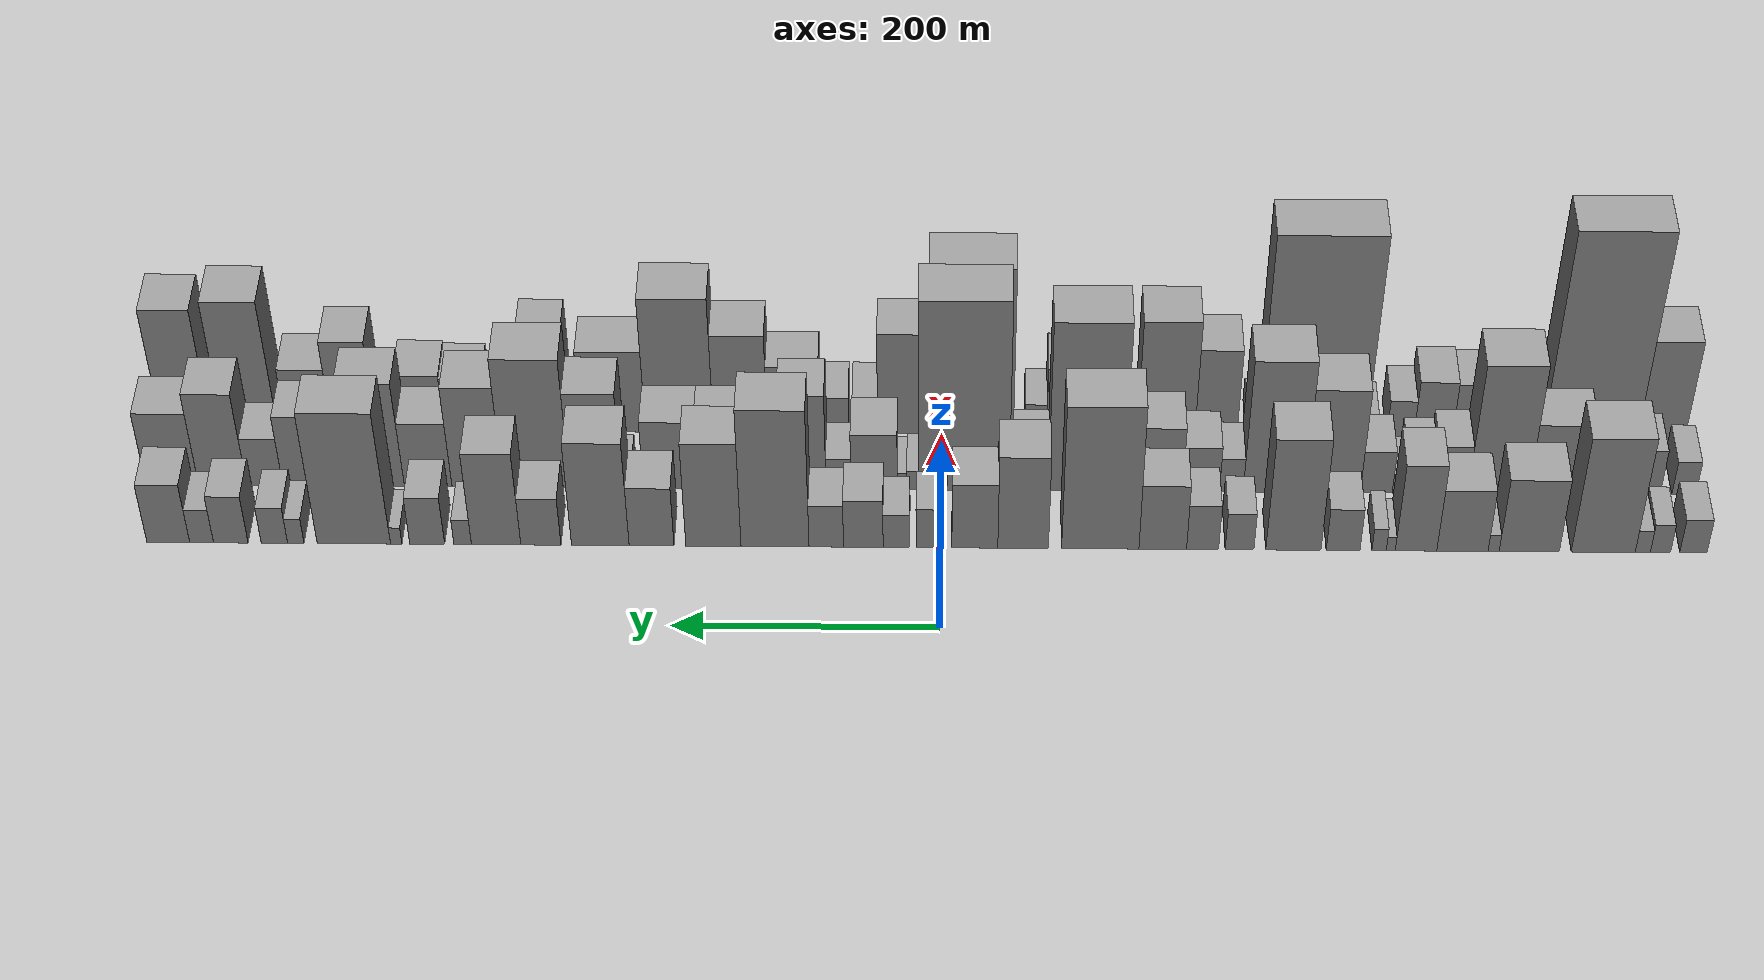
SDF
<sdf version="1.6">
 <world name="default">
  <scene>
   <sky><clouds><speed>12</speed></clouds></sky>
   <ambient>0.4 0.4 0.4 1</ambient>
   <background>0.7 0.7 0.7 1</background>
   <shadows>1</shadows>
  </scene>
  <gravity>0 0 -9.8066</gravity>
  <magnetic_field>6e-06 2.3e-05 -4.2e-05</magnetic_field>
  <physics default="0" name="default_physics" type="ode">
   <ode>
    <solver>
     <type>quick</type>
     <iters>10</iters>
     <sor>1.0</sor>
     <use_dynamic_moi_rescaling>0</use_dynamic_moi_rescaling>
    </solver>
    <constraints>
     <cfm>0</cfm>
     <erp>0.2</erp>
     <contact_max_correcting_vel>100</contact_max_correcting_vel>
     <contact_surface_layer>0.001</contact_surface_layer>
    </constraints>
   </ode>
   <max_step_size>0.004</max_step_size>
   <real_time_factor>1</real_time_factor>
   <real_time_update_rate>250</real_time_update_rate>
  </physics>
  <light name="sun" type="directional">
   <pose>0 0 10 0 0 0</pose>
   <diffuse>0.8 0.8 0.8 1</diffuse>
   <specular>0.2 0.2 0.2 1</specular>
   <attenuation>
    <range>1000</range>
    <constant>0.9</constant>
    <linear>0.01</linear>
    <quadratic>0.001</quadratic>
   </attenuation>
   <direction>-0.5 0.1 -0.9</direction>
  </light>
  <model name="building_1">
   <static>1</static>
   <pose>100.0000 -569.7294 0 0.000000 0.000000 0.000000</pose>
   <link name="link">
    <pose>0 0 18.00 0 0 0</pose>
    <collision name="collision"><geometry><box><size>40.0000 20.5411 36.0000</size></box></geometry></collision>
    <visual name="visual">
     <cast_shadows>0</cast_shadows>
     <geometry><box><size>40.0000 20.5411 36.0000</size></box></geometry>
     <material>
      <script>
       <uri>model://grey_wall/materials/scripts</uri>
       <uri>model://grey_wall/materials/textures</uri>
       <name>vrc/grey_wall</name>
      </script>
     </material>
    </visual>
   </link>
  </model>
  <model name="building_2">
   <static>1</static>
   <pose>100.0000 -544.8365 0 0.000000 0.000000 0.000000</pose>
   <link name="link">
    <pose>0 0 15.00 0 0 0</pose>
    <collision name="collision"><geometry><box><size>40.0000 15.2448 30.0000</size></box></geometry></collision>
    <visual name="visual">
     <cast_shadows>0</cast_shadows>
     <geometry><box><size>40.0000 15.2448 30.0000</size></box></geometry>
     <material>
      <script>
       <uri>model://grey_wall/materials/scripts</uri>
       <uri>model://grey_wall/materials/textures</uri>
       <name>vrc/grey_wall</name>
      </script>
     </material>
    </visual>
   </link>
  </model>
  <model name="building_3">
   <static>1</static>
   <pose>100.0000 -531.4827 0 0.000000 0.000000 0.000000</pose>
   <link name="link">
    <pose>0 0 12.00 0 0 0</pose>
    <collision name="collision"><geometry><box><size>40.0000 11.4627 24.0000</size></box></geometry></collision>
    <visual name="visual">
     <cast_shadows>0</cast_shadows>
     <geometry><box><size>40.0000 11.4627 24.0000</size></box></geometry>
     <material>
      <script>
       <uri>model://grey_wall/materials/scripts</uri>
       <uri>model://grey_wall/materials/textures</uri>
       <name>vrc/grey_wall</name>
      </script>
     </material>
    </visual>
   </link>
  </model>
  <model name="building_4">
   <static>1</static>
   <pose>100.0000 -501.5214 0 0.000000 0.000000 0.000000</pose>
   <link name="link">
    <pose>0 0 61.50 0 0 0</pose>
    <collision name="collision"><geometry><box><size>40.0000 48.4600 123.0000</size></box></geometry></collision>
    <visual name="visual">
     <cast_shadows>0</cast_shadows>
     <geometry><box><size>40.0000 48.4600 123.0000</size></box></geometry>
     <material>
      <script>
       <uri>model://grey_wall/materials/scripts</uri>
       <uri>model://grey_wall/materials/textures</uri>
       <name>vrc/grey_wall</name>
      </script>
     </material>
    </visual>
   </link>
  </model>
  <model name="building_5">
   <static>1</static>
   <pose>100.0000 -445.5409 0 0.000000 0.000000 0.000000</pose>
   <link name="link">
    <pose>0 0 39.00 0 0 0</pose>
    <collision name="collision"><geometry><box><size>40.0000 45.5010 78.0000</size></box></geometry></collision>
    <visual name="visual">
     <cast_shadows>0</cast_shadows>
     <geometry><box><size>40.0000 45.5010 78.0000</size></box></geometry>
     <material>
      <script>
       <uri>model://grey_wall/materials/scripts</uri>
       <uri>model://grey_wall/materials/textures</uri>
       <name>vrc/grey_wall</name>
      </script>
     </material>
    </visual>
   </link>
  </model>
  <model name="building_6">
   <static>1</static>
   <pose>100.0000 -418.5761 0 0.000000 0.000000 0.000000</pose>
   <link name="link">
    <pose>0 0 9.00 0 0 0</pose>
    <collision name="collision"><geometry><box><size>40.0000 8.4285 18.0000</size></box></geometry></collision>
    <visual name="visual">
     <cast_shadows>0</cast_shadows>
     <geometry><box><size>40.0000 8.4285 18.0000</size></box></geometry>
     <material>
      <script>
       <uri>model://grey_wall/materials/scripts</uri>
       <uri>model://grey_wall/materials/textures</uri>
       <name>vrc/grey_wall</name>
      </script>
     </material>
    </visual>
   </link>
  </model>
  <model name="building_7">
   <static>1</static>
   <pose>100.0000 -394.9789 0 0.000000 0.000000 0.000000</pose>
   <link name="link">
    <pose>0 0 33.00 0 0 0</pose>
    <collision name="collision"><geometry><box><size>40.0000 38.7658 66.0000</size></box></geometry></collision>
    <visual name="visual">
     <cast_shadows>0</cast_shadows>
     <geometry><box><size>40.0000 38.7658 66.0000</size></box></geometry>
     <material>
      <script>
       <uri>model://grey_wall/materials/scripts</uri>
       <uri>model://grey_wall/materials/textures</uri>
       <name>vrc/grey_wall</name>
      </script>
     </material>
    </visual>
   </link>
  </model>
  <model name="building_8">
   <static>1</static>
   <pose>100.0000 -359.9123 0 0.000000 0.000000 0.000000</pose>
   <link name="link">
    <pose>0 0 46.50 0 0 0</pose>
    <collision name="collision"><geometry><box><size>40.0000 31.3676 93.0000</size></box></geometry></collision>
    <visual name="visual">
     <cast_shadows>0</cast_shadows>
     <geometry><box><size>40.0000 31.3676 93.0000</size></box></geometry>
     <material>
      <script>
       <uri>model://grey_wall/materials/scripts</uri>
       <uri>model://grey_wall/materials/textures</uri>
       <name>vrc/grey_wall</name>
      </script>
     </material>
    </visual>
   </link>
  </model>
  <model name="building_9">
   <static>1</static>
   <pose>100.0000 -340.8013 0 0.000000 0.000000 0.000000</pose>
   <link name="link">
    <pose>0 0 7.50 0 0 0</pose>
    <collision name="collision"><geometry><box><size>40.0000 6.8542 15.0000</size></box></geometry></collision>
    <visual name="visual">
     <cast_shadows>0</cast_shadows>
     <geometry><box><size>40.0000 6.8542 15.0000</size></box></geometry>
     <material>
      <script>
       <uri>model://grey_wall/materials/scripts</uri>
       <uri>model://grey_wall/materials/textures</uri>
       <name>vrc/grey_wall</name>
      </script>
     </material>
    </visual>
   </link>
  </model>
  <model name="building_10">
   <static>1</static>
   <pose>100.0000 -331.9226 0 0.000000 0.000000 0.000000</pose>
   <link name="link">
    <pose>0 0 12.00 0 0 0</pose>
    <collision name="collision"><geometry><box><size>40.0000 10.9032 24.0000</size></box></geometry></collision>
    <visual name="visual">
     <cast_shadows>0</cast_shadows>
     <geometry><box><size>40.0000 10.9032 24.0000</size></box></geometry>
     <material>
      <script>
       <uri>model://grey_wall/materials/scripts</uri>
       <uri>model://grey_wall/materials/textures</uri>
       <name>vrc/grey_wall</name>
      </script>
     </material>
    </visual>
   </link>
  </model>
  <model name="building_11">
   <static>1</static>
   <pose>100.0000 -304.6821 0 0.000000 0.000000 0.000000</pose>
   <link name="link">
    <pose>0 0 22.50 0 0 0</pose>
    <collision name="collision"><geometry><box><size>40.0000 25.5778 45.0000</size></box></geometry></collision>
    <visual name="visual">
     <cast_shadows>0</cast_shadows>
     <geometry><box><size>40.0000 25.5778 45.0000</size></box></geometry>
     <material>
      <script>
       <uri>model://grey_wall/materials/scripts</uri>
       <uri>model://grey_wall/materials/textures</uri>
       <name>vrc/grey_wall</name>
      </script>
     </material>
    </visual>
   </link>
  </model>
  <model name="building_12">
   <static>1</static>
   <pose>100.0000 -267.0207 0 0.000000 0.000000 0.000000</pose>
   <link name="link">
    <pose>0 0 60.00 0 0 0</pose>
    <collision name="collision"><geometry><box><size>40.0000 41.7449 120.0000</size></box></geometry></collision>
    <visual name="visual">
     <cast_shadows>0</cast_shadows>
     <geometry><box><size>40.0000 41.7449 120.0000</size></box></geometry>
     <material>
      <script>
       <uri>model://grey_wall/materials/scripts</uri>
       <uri>model://grey_wall/materials/textures</uri>
       <name>vrc/grey_wall</name>
      </script>
     </material>
    </visual>
   </link>
  </model>
  <model name="building_13">
   <static>1</static>
   <pose>100.0000 -226.2781 0 0.000000 0.000000 0.000000</pose>
   <link name="link">
    <pose>0 0 19.50 0 0 0</pose>
    <collision name="collision"><geometry><box><size>40.0000 21.7403 39.0000</size></box></geometry></collision>
    <visual name="visual">
     <cast_shadows>0</cast_shadows>
     <geometry><box><size>40.0000 21.7403 39.0000</size></box></geometry>
     <material>
      <script>
       <uri>model://grey_wall/materials/scripts</uri>
       <uri>model://grey_wall/materials/textures</uri>
       <name>vrc/grey_wall</name>
      </script>
     </material>
    </visual>
   </link>
  </model>
  <model name="building_14">
   <static>1</static>
   <pose>100.0000 -198.2800 0 0.000000 0.000000 0.000000</pose>
   <link name="link">
    <pose>0 0 24.00 0 0 0</pose>
    <collision name="collision"><geometry><box><size>40.0000 24.2561 48.0000</size></box></geometry></collision>
    <visual name="visual">
     <cast_shadows>0</cast_shadows>
     <geometry><box><size>40.0000 24.2561 48.0000</size></box></geometry>
     <material>
      <script>
       <uri>model://grey_wall/materials/scripts</uri>
       <uri>model://grey_wall/materials/textures</uri>
       <name>vrc/grey_wall</name>
      </script>
     </material>
    </visual>
   </link>
  </model>
  <model name="building_15">
   <static>1</static>
   <pose>100.0000 -168.1110 0 0.000000 0.000000 0.000000</pose>
   <link name="link">
    <pose>0 0 34.50 0 0 0</pose>
    <collision name="collision"><geometry><box><size>40.0000 36.0818 69.0000</size></box></geometry></collision>
    <visual name="visual">
     <cast_shadows>0</cast_shadows>
     <geometry><box><size>40.0000 36.0818 69.0000</size></box></geometry>
     <material>
      <script>
       <uri>model://grey_wall/materials/scripts</uri>
       <uri>model://grey_wall/materials/textures</uri>
       <name>vrc/grey_wall</name>
      </script>
     </material>
    </visual>
   </link>
  </model>
  <model name="building_16">
   <static>1</static>
   <pose>100.0000 -120.7735 0 0.000000 0.000000 0.000000</pose>
   <link name="link">
    <pose>0 0 76.50 0 0 0</pose>
    <collision name="collision"><geometry><box><size>40.0000 58.5933 153.0000</size></box></geometry></collision>
    <visual name="visual">
     <cast_shadows>0</cast_shadows>
     <geometry><box><size>40.0000 58.5933 153.0000</size></box></geometry>
     <material>
      <script>
       <uri>model://grey_wall/materials/scripts</uri>
       <uri>model://grey_wall/materials/textures</uri>
       <name>vrc/grey_wall</name>
      </script>
     </material>
    </visual>
   </link>
  </model>
  <model name="building_17">
   <static>1</static>
   <pose>100.0000 -62.2903 0 0.000000 0.000000 0.000000</pose>
   <link name="link">
    <pose>0 0 49.50 0 0 0</pose>
    <collision name="collision"><geometry><box><size>40.0000 38.3731 99.0000</size></box></geometry></collision>
    <visual name="visual">
     <cast_shadows>0</cast_shadows>
     <geometry><box><size>40.0000 38.3731 99.0000</size></box></geometry>
     <material>
      <script>
       <uri>model://grey_wall/materials/scripts</uri>
       <uri>model://grey_wall/materials/textures</uri>
       <name>vrc/grey_wall</name>
      </script>
     </material>
    </visual>
   </link>
  </model>
  <model name="building_18">
   <static>1</static>
   <pose>100.0000 -25.6986 0 0.000000 0.000000 0.000000</pose>
   <link name="link">
    <pose>0 0 34.50 0 0 0</pose>
    <collision name="collision"><geometry><box><size>40.0000 34.8102 69.0000</size></box></geometry></collision>
    <visual name="visual">
     <cast_shadows>0</cast_shadows>
     <geometry><box><size>40.0000 34.8102 69.0000</size></box></geometry>
     <material>
      <script>
       <uri>model://grey_wall/materials/scripts</uri>
       <uri>model://grey_wall/materials/textures</uri>
       <name>vrc/grey_wall</name>
      </script>
     </material>
    </visual>
   </link>
  </model>
  <model name="building_19">
   <static>1</static>
   <pose>100.0000 7.2815 0 0.000000 0.000000 0.000000</pose>
   <link name="link">
    <pose>0 0 21.00 0 0 0</pose>
    <collision name="collision"><geometry><box><size>40.0000 23.1501 42.0000</size></box></geometry></collision>
    <visual name="visual">
     <cast_shadows>0</cast_shadows>
     <geometry><box><size>40.0000 23.1501 42.0000</size></box></geometry>
     <material>
      <script>
       <uri>model://grey_wall/materials/scripts</uri>
       <uri>model://grey_wall/materials/textures</uri>
       <name>vrc/grey_wall</name>
      </script>
     </material>
    </visual>
   </link>
  </model>
  <model name="building_20">
   <static>1</static>
   <pose>100.0000 33.8329 0 0.000000 0.000000 0.000000</pose>
   <link name="link">
    <pose>0 0 18.00 0 0 0</pose>
    <collision name="collision"><geometry><box><size>40.0000 19.9525 36.0000</size></box></geometry></collision>
    <visual name="visual">
     <cast_shadows>0</cast_shadows>
     <geometry><box><size>40.0000 19.9525 36.0000</size></box></geometry>
     <material>
      <script>
       <uri>model://grey_wall/materials/scripts</uri>
       <uri>model://grey_wall/materials/textures</uri>
       <name>vrc/grey_wall</name>
      </script>
     </material>
    </visual>
   </link>
  </model>
  <model name="building_21">
   <static>1</static>
   <pose>100.0000 58.8355 0 0.000000 0.000000 0.000000</pose>
   <link name="link">
    <pose>0 0 25.50 0 0 0</pose>
    <collision name="collision"><geometry><box><size>40.0000 30.0528 51.0000</size></box></geometry></collision>
    <visual name="visual">
     <cast_shadows>0</cast_shadows>
     <geometry><box><size>40.0000 30.0528 51.0000</size></box></geometry>
     <material>
      <script>
       <uri>model://grey_wall/materials/scripts</uri>
       <uri>model://grey_wall/materials/textures</uri>
       <name>vrc/grey_wall</name>
      </script>
     </material>
    </visual>
   </link>
  </model>
  <model name="building_22">
   <static>1</static>
   <pose>100.0000 86.9364 0 0.000000 0.000000 0.000000</pose>
   <link name="link">
    <pose>0 0 22.50 0 0 0</pose>
    <collision name="collision"><geometry><box><size>40.0000 26.1490 45.0000</size></box></geometry></collision>
    <visual name="visual">
     <cast_shadows>0</cast_shadows>
     <geometry><box><size>40.0000 26.1490 45.0000</size></box></geometry>
     <material>
      <script>
       <uri>model://grey_wall/materials/scripts</uri>
       <uri>model://grey_wall/materials/textures</uri>
       <name>vrc/grey_wall</name>
      </script>
     </material>
    </visual>
   </link>
  </model>
  <model name="building_23">
   <static>1</static>
   <pose>100.0000 125.7949 0 0.000000 0.000000 0.000000</pose>
   <link name="link">
    <pose>0 0 73.50 0 0 0</pose>
    <collision name="collision"><geometry><box><size>40.0000 51.5680 147.0000</size></box></geometry></collision>
    <visual name="visual">
     <cast_shadows>0</cast_shadows>
     <geometry><box><size>40.0000 51.5680 147.0000</size></box></geometry>
     <material>
      <script>
       <uri>model://grey_wall/materials/scripts</uri>
       <uri>model://grey_wall/materials/textures</uri>
       <name>vrc/grey_wall</name>
      </script>
     </material>
    </visual>
   </link>
  </model>
  <model name="building_24">
   <static>1</static>
   <pose>100.0000 172.5010 0 0.000000 0.000000 0.000000</pose>
   <link name="link">
    <pose>0 0 55.50 0 0 0</pose>
    <collision name="collision"><geometry><box><size>40.0000 41.8441 111.0000</size></box></geometry></collision>
    <visual name="visual">
     <cast_shadows>0</cast_shadows>
     <geometry><box><size>40.0000 41.8441 111.0000</size></box></geometry>
     <material>
      <script>
       <uri>model://grey_wall/materials/scripts</uri>
       <uri>model://grey_wall/materials/textures</uri>
       <name>vrc/grey_wall</name>
      </script>
     </material>
    </visual>
   </link>
  </model>
  <model name="building_25">
   <static>1</static>
   <pose>100.0000 219.4395 0 0.000000 0.000000 0.000000</pose>
   <link name="link">
    <pose>0 0 31.50 0 0 0</pose>
    <collision name="collision"><geometry><box><size>40.0000 34.0330 63.0000</size></box></geometry></collision>
    <visual name="visual">
     <cast_shadows>0</cast_shadows>
     <geometry><box><size>40.0000 34.0330 63.0000</size></box></geometry>
     <material>
      <script>
       <uri>model://grey_wall/materials/scripts</uri>
       <uri>model://grey_wall/materials/textures</uri>
       <name>vrc/grey_wall</name>
      </script>
     </material>
    </visual>
   </link>
  </model>
  <model name="building_26">
   <static>1</static>
   <pose>100.0000 258.3282 0 0.000000 0.000000 0.000000</pose>
   <link name="link">
    <pose>0 0 55.50 0 0 0</pose>
    <collision name="collision"><geometry><box><size>40.0000 43.7445 111.0000</size></box></geometry></collision>
    <visual name="visual">
     <cast_shadows>0</cast_shadows>
     <geometry><box><size>40.0000 43.7445 111.0000</size></box></geometry>
     <material>
      <script>
       <uri>model://grey_wall/materials/scripts</uri>
       <uri>model://grey_wall/materials/textures</uri>
       <name>vrc/grey_wall</name>
      </script>
     </material>
    </visual>
   </link>
  </model>
  <model name="building_27">
   <static>1</static>
   <pose>100.0000 303.4414 0 0.000000 0.000000 0.000000</pose>
   <link name="link">
    <pose>0 0 25.50 0 0 0</pose>
    <collision name="collision"><geometry><box><size>40.0000 30.4819 51.0000</size></box></geometry></collision>
    <visual name="visual">
     <cast_shadows>0</cast_shadows>
     <geometry><box><size>40.0000 30.4819 51.0000</size></box></geometry>
     <material>
      <script>
       <uri>model://grey_wall/materials/scripts</uri>
       <uri>model://grey_wall/materials/textures</uri>
       <name>vrc/grey_wall</name>
      </script>
     </material>
    </visual>
   </link>
  </model>
  <model name="building_28">
   <static>1</static>
   <pose>100.0000 337.4438 0 0.000000 0.000000 0.000000</pose>
   <link name="link">
    <pose>0 0 49.50 0 0 0</pose>
    <collision name="collision"><geometry><box><size>40.0000 37.5230 99.0000</size></box></geometry></collision>
    <visual name="visual">
     <cast_shadows>0</cast_shadows>
     <geometry><box><size>40.0000 37.5230 99.0000</size></box></geometry>
     <material>
      <script>
       <uri>model://grey_wall/materials/scripts</uri>
       <uri>model://grey_wall/materials/textures</uri>
       <name>vrc/grey_wall</name>
      </script>
     </material>
    </visual>
   </link>
  </model>
  <model name="building_29">
   <static>1</static>
   <pose>100.0000 362.8427 0 0.000000 0.000000 0.000000</pose>
   <link name="link">
    <pose>0 0 13.50 0 0 0</pose>
    <collision name="collision"><geometry><box><size>40.0000 13.2747 27.0000</size></box></geometry></collision>
    <visual name="visual">
     <cast_shadows>0</cast_shadows>
     <geometry><box><size>40.0000 13.2747 27.0000</size></box></geometry>
     <material>
      <script>
       <uri>model://grey_wall/materials/scripts</uri>
       <uri>model://grey_wall/materials/textures</uri>
       <name>vrc/grey_wall</name>
      </script>
     </material>
    </visual>
   </link>
  </model>
  <model name="building_30">
   <static>1</static>
   <pose>100.0000 389.7202 0 0.000000 0.000000 0.000000</pose>
   <link name="link">
    <pose>0 0 25.50 0 0 0</pose>
    <collision name="collision"><geometry><box><size>40.0000 26.4803 51.0000</size></box></geometry></collision>
    <visual name="visual">
     <cast_shadows>0</cast_shadows>
     <geometry><box><size>40.0000 26.4803 51.0000</size></box></geometry>
     <material>
      <script>
       <uri>model://grey_wall/materials/scripts</uri>
       <uri>model://grey_wall/materials/textures</uri>
       <name>vrc/grey_wall</name>
      </script>
     </material>
    </visual>
   </link>
  </model>
  <model name="building_31">
   <static>1</static>
   <pose>100.0000 413.2818 0 0.000000 0.000000 0.000000</pose>
   <link name="link">
    <pose>0 0 9.00 0 0 0</pose>
    <collision name="collision"><geometry><box><size>40.0000 8.6429 18.0000</size></box></geometry></collision>
    <visual name="visual">
     <cast_shadows>0</cast_shadows>
     <geometry><box><size>40.0000 8.6429 18.0000</size></box></geometry>
     <material>
      <script>
       <uri>model://grey_wall/materials/scripts</uri>
       <uri>model://grey_wall/materials/textures</uri>
       <name>vrc/grey_wall</name>
      </script>
     </material>
    </visual>
   </link>
  </model>
  <model name="building_32">
   <static>1</static>
   <pose>100.0000 445.4660 0 0.000000 0.000000 0.000000</pose>
   <link name="link">
    <pose>0 0 70.50 0 0 0</pose>
    <collision name="collision"><geometry><box><size>40.0000 55.7255 141.0000</size></box></geometry></collision>
    <visual name="visual">
     <cast_shadows>0</cast_shadows>
     <geometry><box><size>40.0000 55.7255 141.0000</size></box></geometry>
     <material>
      <script>
       <uri>model://grey_wall/materials/scripts</uri>
       <uri>model://grey_wall/materials/textures</uri>
       <name>vrc/grey_wall</name>
      </script>
     </material>
    </visual>
   </link>
  </model>
  <model name="building_33">
   <static>1</static>
   <pose>100.0000 489.5801 0 0.000000 0.000000 0.000000</pose>
   <link name="link">
    <pose>0 0 13.50 0 0 0</pose>
    <collision name="collision"><geometry><box><size>40.0000 12.5028 27.0000</size></box></geometry></collision>
    <visual name="visual">
     <cast_shadows>0</cast_shadows>
     <geometry><box><size>40.0000 12.5028 27.0000</size></box></geometry>
     <material>
      <script>
       <uri>model://grey_wall/materials/scripts</uri>
       <uri>model://grey_wall/materials/textures</uri>
       <name>vrc/grey_wall</name>
      </script>
     </material>
    </visual>
   </link>
  </model>
  <model name="building_34">
   <static>1</static>
   <pose>100.0000 505.8345 0 0.000000 0.000000 0.000000</pose>
   <link name="link">
    <pose>0 0 19.50 0 0 0</pose>
    <collision name="collision"><geometry><box><size>40.0000 20.0061 39.0000</size></box></geometry></collision>
    <visual name="visual">
     <cast_shadows>0</cast_shadows>
     <geometry><box><size>40.0000 20.0061 39.0000</size></box></geometry>
     <material>
      <script>
       <uri>model://grey_wall/materials/scripts</uri>
       <uri>model://grey_wall/materials/textures</uri>
       <name>vrc/grey_wall</name>
      </script>
     </material>
    </visual>
   </link>
  </model>
  <model name="building_35">
   <static>1</static>
   <pose>100.0000 538.9718 0 0.000000 0.000000 0.000000</pose>
   <link name="link">
    <pose>0 0 25.50 0 0 0</pose>
    <collision name="collision"><geometry><box><size>40.0000 26.2685 51.0000</size></box></geometry></collision>
    <visual name="visual">
     <cast_shadows>0</cast_shadows>
     <geometry><box><size>40.0000 26.2685 51.0000</size></box></geometry>
     <material>
      <script>
       <uri>model://grey_wall/materials/scripts</uri>
       <uri>model://grey_wall/materials/textures</uri>
       <name>vrc/grey_wall</name>
      </script>
     </material>
    </visual>
   </link>
  </model>
  <model name="building_36">
   <static>1</static>
   <pose>100.0000 561.1480 0 0.000000 0.000000 0.000000</pose>
   <link name="link">
    <pose>0 0 18.00 0 0 0</pose>
    <collision name="collision"><geometry><box><size>40.0000 18.0839 36.0000</size></box></geometry></collision>
    <visual name="visual">
     <cast_shadows>0</cast_shadows>
     <geometry><box><size>40.0000 18.0839 36.0000</size></box></geometry>
     <material>
      <script>
       <uri>model://grey_wall/materials/scripts</uri>
       <uri>model://grey_wall/materials/textures</uri>
       <name>vrc/grey_wall</name>
      </script>
     </material>
    </visual>
   </link>
  </model>
  <model name="building_37">
   <static>1</static>
   <pose>100.0000 586.4755 0 0.000000 0.000000 0.000000</pose>
   <link name="link">
    <pose>0 0 31.50 0 0 0</pose>
    <collision name="collision"><geometry><box><size>40.0000 32.5711 63.0000</size></box></geometry></collision>
    <visual name="visual">
     <cast_shadows>0</cast_shadows>
     <geometry><box><size>40.0000 32.5711 63.0000</size></box></geometry>
     <material>
      <script>
       <uri>model://grey_wall/materials/scripts</uri>
       <uri>model://grey_wall/materials/textures</uri>
       <name>vrc/grey_wall</name>
      </script>
     </material>
    </visual>
   </link>
  </model>
  <model name="building_38">
   <static>1</static>
   <pose>160.0000 -570.8208 0 0.000000 0.000000 0.000000</pose>
   <link name="link">
    <pose>0 0 18.00 0 0 0</pose>
    <collision name="collision"><geometry><box><size>40.0000 18.3584 36.0000</size></box></geometry></collision>
    <visual name="visual">
     <cast_shadows>0</cast_shadows>
     <geometry><box><size>40.0000 18.3584 36.0000</size></box></geometry>
     <material>
      <script>
       <uri>model://grey_wall/materials/scripts</uri>
       <uri>model://grey_wall/materials/textures</uri>
       <name>vrc/grey_wall</name>
      </script>
     </material>
    </visual>
   </link>
  </model>
  <model name="building_39">
   <static>1</static>
   <pose>160.0000 -539.3409 0 0.000000 0.000000 0.000000</pose>
   <link name="link">
    <pose>0 0 24.00 0 0 0</pose>
    <collision name="collision"><geometry><box><size>40.0000 26.6013 48.0000</size></box></geometry></collision>
    <visual name="visual">
     <cast_shadows>0</cast_shadows>
     <geometry><box><size>40.0000 26.6013 48.0000</size></box></geometry>
     <material>
      <script>
       <uri>model://grey_wall/materials/scripts</uri>
       <uri>model://grey_wall/materials/textures</uri>
       <name>vrc/grey_wall</name>
      </script>
     </material>
    </visual>
   </link>
  </model>
  <model name="building_40">
   <static>1</static>
   <pose>160.0000 -506.1408 0 0.000000 0.000000 0.000000</pose>
   <link name="link">
    <pose>0 0 18.00 0 0 0</pose>
    <collision name="collision"><geometry><box><size>40.0000 19.7989 36.0000</size></box></geometry></collision>
    <visual name="visual">
     <cast_shadows>0</cast_shadows>
     <geometry><box><size>40.0000 19.7989 36.0000</size></box></geometry>
     <material>
      <script>
       <uri>model://grey_wall/materials/scripts</uri>
       <uri>model://grey_wall/materials/textures</uri>
       <name>vrc/grey_wall</name>
      </script>
     </material>
    </visual>
   </link>
  </model>
  <model name="building_41">
   <static>1</static>
   <pose>160.0000 -473.7672 0 0.000000 0.000000 0.000000</pose>
   <link name="link">
    <pose>0 0 37.50 0 0 0</pose>
    <collision name="collision"><geometry><box><size>40.0000 44.9482 75.0000</size></box></geometry></collision>
    <visual name="visual">
     <cast_shadows>0</cast_shadows>
     <geometry><box><size>40.0000 44.9482 75.0000</size></box></geometry>
     <material>
      <script>
       <uri>model://grey_wall/materials/scripts</uri>
       <uri>model://grey_wall/materials/textures</uri>
       <name>vrc/grey_wall</name>
      </script>
     </material>
    </visual>
   </link>
  </model>
  <model name="building_42">
   <static>1</static>
   <pose>160.0000 -428.0473 0 0.000000 0.000000 0.000000</pose>
   <link name="link">
    <pose>0 0 69.00 0 0 0</pose>
    <collision name="collision"><geometry><box><size>40.0000 46.4916 138.0000</size></box></geometry></collision>
    <visual name="visual">
     <cast_shadows>0</cast_shadows>
     <geometry><box><size>40.0000 46.4916 138.0000</size></box></geometry>
     <material>
      <script>
       <uri>model://grey_wall/materials/scripts</uri>
       <uri>model://grey_wall/materials/textures</uri>
       <name>vrc/grey_wall</name>
      </script>
     </material>
    </visual>
   </link>
  </model>
  <model name="building_43">
   <static>1</static>
   <pose>160.0000 -391.6803 0 0.000000 0.000000 0.000000</pose>
   <link name="link">
    <pose>0 0 25.50 0 0 0</pose>
    <collision name="collision"><geometry><box><size>40.0000 26.2424 51.0000</size></box></geometry></collision>
    <visual name="visual">
     <cast_shadows>0</cast_shadows>
     <geometry><box><size>40.0000 26.2424 51.0000</size></box></geometry>
     <material>
      <script>
       <uri>model://grey_wall/materials/scripts</uri>
       <uri>model://grey_wall/materials/textures</uri>
       <name>vrc/grey_wall</name>
      </script>
     </material>
    </visual>
   </link>
  </model>
  <model name="building_44">
   <static>1</static>
   <pose>160.0000 -366.9874 0 0.000000 0.000000 0.000000</pose>
   <link name="link">
    <pose>0 0 21.00 0 0 0</pose>
    <collision name="collision"><geometry><box><size>40.0000 23.1434 42.0000</size></box></geometry></collision>
    <visual name="visual">
     <cast_shadows>0</cast_shadows>
     <geometry><box><size>40.0000 23.1434 42.0000</size></box></geometry>
     <material>
      <script>
       <uri>model://grey_wall/materials/scripts</uri>
       <uri>model://grey_wall/materials/textures</uri>
       <name>vrc/grey_wall</name>
      </script>
     </material>
    </visual>
   </link>
  </model>
  <model name="building_45">
   <static>1</static>
   <pose>160.0000 -351.0941 0 0.000000 0.000000 0.000000</pose>
   <link name="link">
    <pose>0 0 10.50 0 0 0</pose>
    <collision name="collision"><geometry><box><size>40.0000 8.6432 21.0000</size></box></geometry></collision>
    <visual name="visual">
     <cast_shadows>0</cast_shadows>
     <geometry><box><size>40.0000 8.6432 21.0000</size></box></geometry>
     <material>
      <script>
       <uri>model://grey_wall/materials/scripts</uri>
       <uri>model://grey_wall/materials/textures</uri>
       <name>vrc/grey_wall</name>
      </script>
     </material>
    </visual>
   </link>
  </model>
  <model name="building_46">
   <static>1</static>
   <pose>160.0000 -334.4857 0 0.000000 0.000000 0.000000</pose>
   <link name="link">
    <pose>0 0 22.50 0 0 0</pose>
    <collision name="collision"><geometry><box><size>40.0000 24.5735 45.0000</size></box></geometry></collision>
    <visual name="visual">
     <cast_shadows>0</cast_shadows>
     <geometry><box><size>40.0000 24.5735 45.0000</size></box></geometry>
     <material>
      <script>
       <uri>model://grey_wall/materials/scripts</uri>
       <uri>model://grey_wall/materials/textures</uri>
       <name>vrc/grey_wall</name>
      </script>
     </material>
    </visual>
   </link>
  </model>
  <model name="building_47">
   <static>1</static>
   <pose>160.0000 -301.0077 0 0.000000 0.000000 0.000000</pose>
   <link name="link">
    <pose>0 0 55.50 0 0 0</pose>
    <collision name="collision"><geometry><box><size>40.0000 42.3825 111.0000</size></box></geometry></collision>
    <visual name="visual">
     <cast_shadows>0</cast_shadows>
     <geometry><box><size>40.0000 42.3825 111.0000</size></box></geometry>
     <material>
      <script>
       <uri>model://grey_wall/materials/scripts</uri>
       <uri>model://grey_wall/materials/textures</uri>
       <name>vrc/grey_wall</name>
      </script>
     </material>
    </visual>
   </link>
  </model>
  <model name="building_48">
   <static>1</static>
   <pose>160.0000 -256.0174 0 0.000000 0.000000 0.000000</pose>
   <link name="link">
    <pose>0 0 70.50 0 0 0</pose>
    <collision name="collision"><geometry><box><size>40.0000 47.5980 141.0000</size></box></geometry></collision>
    <visual name="visual">
     <cast_shadows>0</cast_shadows>
     <geometry><box><size>40.0000 47.5980 141.0000</size></box></geometry>
     <material>
      <script>
       <uri>model://grey_wall/materials/scripts</uri>
       <uri>model://grey_wall/materials/textures</uri>
       <name>vrc/grey_wall</name>
      </script>
     </material>
    </visual>
   </link>
  </model>
  <model name="building_49">
   <static>1</static>
   <pose>160.0000 -223.1073 0 0.000000 0.000000 0.000000</pose>
   <link name="link">
    <pose>0 0 18.00 0 0 0</pose>
    <collision name="collision"><geometry><box><size>40.0000 18.2224 36.0000</size></box></geometry></collision>
    <visual name="visual">
     <cast_shadows>0</cast_shadows>
     <geometry><box><size>40.0000 18.2224 36.0000</size></box></geometry>
     <material>
      <script>
       <uri>model://grey_wall/materials/scripts</uri>
       <uri>model://grey_wall/materials/textures</uri>
       <name>vrc/grey_wall</name>
      </script>
     </material>
    </visual>
   </link>
  </model>
  <model name="building_50">
   <static>1</static>
   <pose>160.0000 -199.8318 0 0.000000 0.000000 0.000000</pose>
   <link name="link">
    <pose>0 0 24.00 0 0 0</pose>
    <collision name="collision"><geometry><box><size>40.0000 28.3286 48.0000</size></box></geometry></collision>
    <visual name="visual">
     <cast_shadows>0</cast_shadows>
     <geometry><box><size>40.0000 28.3286 48.0000</size></box></geometry>
     <material>
      <script>
       <uri>model://grey_wall/materials/scripts</uri>
       <uri>model://grey_wall/materials/textures</uri>
       <name>vrc/grey_wall</name>
      </script>
     </material>
    </visual>
   </link>
  </model>
  <model name="building_51">
   <static>1</static>
   <pose>160.0000 -166.2779 0 0.000000 0.000000 0.000000</pose>
   <link name="link">
    <pose>0 0 34.50 0 0 0</pose>
    <collision name="collision"><geometry><box><size>40.0000 38.7792 69.0000</size></box></geometry></collision>
    <visual name="visual">
     <cast_shadows>0</cast_shadows>
     <geometry><box><size>40.0000 38.7792 69.0000</size></box></geometry>
     <material>
      <script>
       <uri>model://grey_wall/materials/scripts</uri>
       <uri>model://grey_wall/materials/textures</uri>
       <name>vrc/grey_wall</name>
      </script>
     </material>
    </visual>
   </link>
  </model>
  <model name="building_52">
   <static>1</static>
   <pose>160.0000 -111.5889 0 0.000000 0.000000 0.000000</pose>
   <link name="link">
    <pose>0 0 90.00 0 0 0</pose>
    <collision name="collision"><geometry><box><size>40.0000 58.5987 180.0000</size></box></geometry></collision>
    <visual name="visual">
     <cast_shadows>0</cast_shadows>
     <geometry><box><size>40.0000 58.5987 180.0000</size></box></geometry>
     <material>
      <script>
       <uri>model://grey_wall/materials/scripts</uri>
       <uri>model://grey_wall/materials/textures</uri>
       <name>vrc/grey_wall</name>
      </script>
     </material>
    </visual>
   </link>
  </model>
  <model name="building_53">
   <static>1</static>
   <pose>160.0000 -68.7185 0 0.000000 0.000000 0.000000</pose>
   <link name="link">
    <pose>0 0 24.00 0 0 0</pose>
    <collision name="collision"><geometry><box><size>40.0000 27.1422 48.0000</size></box></geometry></collision>
    <visual name="visual">
     <cast_shadows>0</cast_shadows>
     <geometry><box><size>40.0000 27.1422 48.0000</size></box></geometry>
     <material>
      <script>
       <uri>model://grey_wall/materials/scripts</uri>
       <uri>model://grey_wall/materials/textures</uri>
       <name>vrc/grey_wall</name>
      </script>
     </material>
    </visual>
   </link>
  </model>
  <model name="building_54">
   <static>1</static>
   <pose>160.0000 -17.2228 0 0.000000 0.000000 0.000000</pose>
   <link name="link">
    <pose>0 0 100.50 0 0 0</pose>
    <collision name="collision"><geometry><box><size>40.0000 69.8490 201.0000</size></box></geometry></collision>
    <visual name="visual">
     <cast_shadows>0</cast_shadows>
     <geometry><box><size>40.0000 69.8490 201.0000</size></box></geometry>
     <material>
      <script>
       <uri>model://grey_wall/materials/scripts</uri>
       <uri>model://grey_wall/materials/textures</uri>
       <name>vrc/grey_wall</name>
      </script>
     </material>
    </visual>
   </link>
  </model>
  <model name="building_55">
   <static>1</static>
   <pose>160.0000 22.1723 0 0.000000 0.000000 0.000000</pose>
   <link name="link">
    <pose>0 0 10.50 0 0 0</pose>
    <collision name="collision"><geometry><box><size>40.0000 8.9414 21.0000</size></box></geometry></collision>
    <visual name="visual">
     <cast_shadows>0</cast_shadows>
     <geometry><box><size>40.0000 8.9414 21.0000</size></box></geometry>
     <material>
      <script>
       <uri>model://grey_wall/materials/scripts</uri>
       <uri>model://grey_wall/materials/textures</uri>
       <name>vrc/grey_wall</name>
      </script>
     </material>
    </visual>
   </link>
  </model>
  <model name="building_56">
   <static>1</static>
   <pose>160.0000 30.2713 0 0.000000 0.000000 0.000000</pose>
   <link name="link">
    <pose>0 0 9.00 0 0 0</pose>
    <collision name="collision"><geometry><box><size>40.0000 7.2566 18.0000</size></box></geometry></collision>
    <visual name="visual">
     <cast_shadows>0</cast_shadows>
     <geometry><box><size>40.0000 7.2566 18.0000</size></box></geometry>
     <material>
      <script>
       <uri>model://grey_wall/materials/scripts</uri>
       <uri>model://grey_wall/materials/textures</uri>
       <name>vrc/grey_wall</name>
      </script>
     </material>
    </visual>
   </link>
  </model>
  <model name="building_57">
   <static>1</static>
   <pose>160.0000 51.7332 0 0.000000 0.000000 0.000000</pose>
   <link name="link">
    <pose>0 0 30.00 0 0 0</pose>
    <collision name="collision"><geometry><box><size>40.0000 35.6672 60.0000</size></box></geometry></collision>
    <visual name="visual">
     <cast_shadows>0</cast_shadows>
     <geometry><box><size>40.0000 35.6672 60.0000</size></box></geometry>
     <material>
      <script>
       <uri>model://grey_wall/materials/scripts</uri>
       <uri>model://grey_wall/materials/textures</uri>
       <name>vrc/grey_wall</name>
      </script>
     </material>
    </visual>
   </link>
  </model>
  <model name="building_58">
   <static>1</static>
   <pose>160.0000 79.1567 0 0.000000 0.000000 0.000000</pose>
   <link name="link">
    <pose>0 0 16.50 0 0 0</pose>
    <collision name="collision"><geometry><box><size>40.0000 19.1798 33.0000</size></box></geometry></collision>
    <visual name="visual">
     <cast_shadows>0</cast_shadows>
     <geometry><box><size>40.0000 19.1798 33.0000</size></box></geometry>
     <material>
      <script>
       <uri>model://grey_wall/materials/scripts</uri>
       <uri>model://grey_wall/materials/textures</uri>
       <name>vrc/grey_wall</name>
      </script>
     </material>
    </visual>
   </link>
  </model>
  <model name="building_59">
   <static>1</static>
   <pose>160.0000 106.7141 0 0.000000 0.000000 0.000000</pose>
   <link name="link">
    <pose>0 0 51.00 0 0 0</pose>
    <collision name="collision"><geometry><box><size>40.0000 35.9351 102.0000</size></box></geometry></collision>
    <visual name="visual">
     <cast_shadows>0</cast_shadows>
     <geometry><box><size>40.0000 35.9351 102.0000</size></box></geometry>
     <material>
      <script>
       <uri>model://grey_wall/materials/scripts</uri>
       <uri>model://grey_wall/materials/textures</uri>
       <name>vrc/grey_wall</name>
      </script>
     </material>
    </visual>
   </link>
  </model>
  <model name="building_60">
   <static>1</static>
   <pose>160.0000 133.5646 0 0.000000 0.000000 0.000000</pose>
   <link name="link">
    <pose>0 0 15.00 0 0 0</pose>
    <collision name="collision"><geometry><box><size>40.0000 17.7658 30.0000</size></box></geometry></collision>
    <visual name="visual">
     <cast_shadows>0</cast_shadows>
     <geometry><box><size>40.0000 17.7658 30.0000</size></box></geometry>
     <material>
      <script>
       <uri>model://grey_wall/materials/scripts</uri>
       <uri>model://grey_wall/materials/textures</uri>
       <name>vrc/grey_wall</name>
      </script>
     </material>
    </visual>
   </link>
  </model>
  <model name="building_61">
   <static>1</static>
   <pose>160.0000 167.3708 0 0.000000 0.000000 0.000000</pose>
   <link name="link">
    <pose>0 0 36.00 0 0 0</pose>
    <collision name="collision"><geometry><box><size>40.0000 41.8467 72.0000</size></box></geometry></collision>
    <visual name="visual">
     <cast_shadows>0</cast_shadows>
     <geometry><box><size>40.0000 41.8467 72.0000</size></box></geometry>
     <material>
      <script>
       <uri>model://grey_wall/materials/scripts</uri>
       <uri>model://grey_wall/materials/textures</uri>
       <name>vrc/grey_wall</name>
      </script>
     </material>
    </visual>
   </link>
  </model>
  <model name="building_62">
   <static>1</static>
   <pose>160.0000 208.8437 0 0.000000 0.000000 0.000000</pose>
   <link name="link">
    <pose>0 0 36.00 0 0 0</pose>
    <collision name="collision"><geometry><box><size>40.0000 41.0991 72.0000</size></box></geometry></collision>
    <visual name="visual">
     <cast_shadows>0</cast_shadows>
     <geometry><box><size>40.0000 41.0991 72.0000</size></box></geometry>
     <material>
      <script>
       <uri>model://grey_wall/materials/scripts</uri>
       <uri>model://grey_wall/materials/textures</uri>
       <name>vrc/grey_wall</name>
      </script>
     </material>
    </visual>
   </link>
  </model>
  <model name="building_63">
   <static>1</static>
   <pose>160.0000 242.2658 0 0.000000 0.000000 0.000000</pose>
   <link name="link">
    <pose>0 0 9.00 0 0 0</pose>
    <collision name="collision"><geometry><box><size>40.0000 7.7452 18.0000</size></box></geometry></collision>
    <visual name="visual">
     <cast_shadows>0</cast_shadows>
     <geometry><box><size>40.0000 7.7452 18.0000</size></box></geometry>
     <material>
      <script>
       <uri>model://grey_wall/materials/scripts</uri>
       <uri>model://grey_wall/materials/textures</uri>
       <name>vrc/grey_wall</name>
      </script>
     </material>
    </visual>
   </link>
  </model>
  <model name="building_64">
   <static>1</static>
   <pose>160.0000 266.1142 0 0.000000 0.000000 0.000000</pose>
   <link name="link">
    <pose>0 0 51.00 0 0 0</pose>
    <collision name="collision"><geometry><box><size>40.0000 39.9515 102.0000</size></box></geometry></collision>
    <visual name="visual">
     <cast_shadows>0</cast_shadows>
     <geometry><box><size>40.0000 39.9515 102.0000</size></box></geometry>
     <material>
      <script>
       <uri>model://grey_wall/materials/scripts</uri>
       <uri>model://grey_wall/materials/textures</uri>
       <name>vrc/grey_wall</name>
      </script>
     </material>
    </visual>
   </link>
  </model>
  <model name="building_65">
   <static>1</static>
   <pose>160.0000 311.8025 0 0.000000 0.000000 0.000000</pose>
   <link name="link">
    <pose>0 0 69.00 0 0 0</pose>
    <collision name="collision"><geometry><box><size>40.0000 51.4252 138.0000</size></box></geometry></collision>
    <visual name="visual">
     <cast_shadows>0</cast_shadows>
     <geometry><box><size>40.0000 51.4252 138.0000</size></box></geometry>
     <material>
      <script>
       <uri>model://grey_wall/materials/scripts</uri>
       <uri>model://grey_wall/materials/textures</uri>
       <name>vrc/grey_wall</name>
      </script>
     </material>
    </visual>
   </link>
  </model>
  <model name="building_66">
   <static>1</static>
   <pose>160.0000 357.2261 0 0.000000 0.000000 0.000000</pose>
   <link name="link">
    <pose>0 0 54.00 0 0 0</pose>
    <collision name="collision"><geometry><box><size>40.0000 39.4219 108.0000</size></box></geometry></collision>
    <visual name="visual">
     <cast_shadows>0</cast_shadows>
     <geometry><box><size>40.0000 39.4219 108.0000</size></box></geometry>
     <material>
      <script>
       <uri>model://grey_wall/materials/scripts</uri>
       <uri>model://grey_wall/materials/textures</uri>
       <name>vrc/grey_wall</name>
      </script>
     </material>
    </visual>
   </link>
  </model>
  <model name="building_67">
   <static>1</static>
   <pose>160.0000 395.2734 0 0.000000 0.000000 0.000000</pose>
   <link name="link">
    <pose>0 0 34.50 0 0 0</pose>
    <collision name="collision"><geometry><box><size>40.0000 36.6727 69.0000</size></box></geometry></collision>
    <visual name="visual">
     <cast_shadows>0</cast_shadows>
     <geometry><box><size>40.0000 36.6727 69.0000</size></box></geometry>
     <material>
      <script>
       <uri>model://grey_wall/materials/scripts</uri>
       <uri>model://grey_wall/materials/textures</uri>
       <name>vrc/grey_wall</name>
      </script>
     </material>
    </visual>
   </link>
  </model>
  <model name="building_68">
   <static>1</static>
   <pose>160.0000 435.0414 0 0.000000 0.000000 0.000000</pose>
   <link name="link">
    <pose>0 0 55.50 0 0 0</pose>
    <collision name="collision"><geometry><box><size>40.0000 42.8633 111.0000</size></box></geometry></collision>
    <visual name="visual">
     <cast_shadows>0</cast_shadows>
     <geometry><box><size>40.0000 42.8633 111.0000</size></box></geometry>
     <material>
      <script>
       <uri>model://grey_wall/materials/scripts</uri>
       <uri>model://grey_wall/materials/textures</uri>
       <name>vrc/grey_wall</name>
      </script>
     </material>
    </visual>
   </link>
  </model>
  <model name="building_69">
   <static>1</static>
   <pose>160.0000 460.9383 0 0.000000 0.000000 0.000000</pose>
   <link name="link">
    <pose>0 0 10.50 0 0 0</pose>
    <collision name="collision"><geometry><box><size>40.0000 8.9306 21.0000</size></box></geometry></collision>
    <visual name="visual">
     <cast_shadows>0</cast_shadows>
     <geometry><box><size>40.0000 8.9306 21.0000</size></box></geometry>
     <material>
      <script>
       <uri>model://grey_wall/materials/scripts</uri>
       <uri>model://grey_wall/materials/textures</uri>
       <name>vrc/grey_wall</name>
      </script>
     </material>
    </visual>
   </link>
  </model>
  <model name="building_70">
   <static>1</static>
   <pose>160.0000 486.3875 0 0.000000 0.000000 0.000000</pose>
   <link name="link">
    <pose>0 0 37.50 0 0 0</pose>
    <collision name="collision"><geometry><box><size>40.0000 41.9678 75.0000</size></box></geometry></collision>
    <visual name="visual">
     <cast_shadows>0</cast_shadows>
     <geometry><box><size>40.0000 41.9678 75.0000</size></box></geometry>
     <material>
      <script>
       <uri>model://grey_wall/materials/scripts</uri>
       <uri>model://grey_wall/materials/textures</uri>
       <name>vrc/grey_wall</name>
      </script>
     </material>
    </visual>
   </link>
  </model>
  <model name="building_71">
   <static>1</static>
   <pose>160.0000 521.3006 0 0.000000 0.000000 0.000000</pose>
   <link name="link">
    <pose>0 0 25.50 0 0 0</pose>
    <collision name="collision"><geometry><box><size>40.0000 27.8584 51.0000</size></box></geometry></collision>
    <visual name="visual">
     <cast_shadows>0</cast_shadows>
     <geometry><box><size>40.0000 27.8584 51.0000</size></box></geometry>
     <material>
      <script>
       <uri>model://grey_wall/materials/scripts</uri>
       <uri>model://grey_wall/materials/textures</uri>
       <name>vrc/grey_wall</name>
      </script>
     </material>
    </visual>
   </link>
  </model>
  <model name="building_72">
   <static>1</static>
   <pose>160.0000 553.8544 0 0.000000 0.000000 0.000000</pose>
   <link name="link">
    <pose>0 0 49.50 0 0 0</pose>
    <collision name="collision"><geometry><box><size>40.0000 37.2492 99.0000</size></box></geometry></collision>
    <visual name="visual">
     <cast_shadows>0</cast_shadows>
     <geometry><box><size>40.0000 37.2492 99.0000</size></box></geometry>
     <material>
      <script>
       <uri>model://grey_wall/materials/scripts</uri>
       <uri>model://grey_wall/materials/textures</uri>
       <name>vrc/grey_wall</name>
      </script>
     </material>
    </visual>
   </link>
  </model>
  <model name="building_73">
   <static>1</static>
   <pose>160.0000 592.7865 0 0.000000 0.000000 0.000000</pose>
   <link name="link">
    <pose>0 0 39.00 0 0 0</pose>
    <collision name="collision"><geometry><box><size>40.0000 40.6149 78.0000</size></box></geometry></collision>
    <visual name="visual">
     <cast_shadows>0</cast_shadows>
     <geometry><box><size>40.0000 40.6149 78.0000</size></box></geometry>
     <material>
      <script>
       <uri>model://grey_wall/materials/scripts</uri>
       <uri>model://grey_wall/materials/textures</uri>
       <name>vrc/grey_wall</name>
      </script>
     </material>
    </visual>
   </link>
  </model>
  <model name="building_74">
   <static>1</static>
   <pose>220.0000 -561.5091 0 0.000000 0.000000 0.000000</pose>
   <link name="link">
    <pose>0 0 52.50 0 0 0</pose>
    <collision name="collision"><geometry><box><size>40.0000 36.9817 105.0000</size></box></geometry></collision>
    <visual name="visual">
     <cast_shadows>0</cast_shadows>
     <geometry><box><size>40.0000 36.9817 105.0000</size></box></geometry>
     <material>
      <script>
       <uri>model://grey_wall/materials/scripts</uri>
       <uri>model://grey_wall/materials/textures</uri>
       <name>vrc/grey_wall</name>
      </script>
     </material>
    </visual>
   </link>
  </model>
  <model name="building_75">
   <static>1</static>
   <pose>220.0000 -505.9745 0 0.000000 0.000000 0.000000</pose>
   <link name="link">
    <pose>0 0 109.50 0 0 0</pose>
    <collision name="collision"><geometry><box><size>40.0000 74.0875 219.0000</size></box></geometry></collision>
    <visual name="visual">
     <cast_shadows>0</cast_shadows>
     <geometry><box><size>40.0000 74.0875 219.0000</size></box></geometry>
     <material>
      <script>
       <uri>model://grey_wall/materials/scripts</uri>
       <uri>model://grey_wall/materials/textures</uri>
       <name>vrc/grey_wall</name>
      </script>
     </material>
    </visual>
   </link>
  </model>
  <model name="building_76">
   <static>1</static>
   <pose>220.0000 -446.1787 0 0.000000 0.000000 0.000000</pose>
   <link name="link">
    <pose>0 0 31.50 0 0 0</pose>
    <collision name="collision"><geometry><box><size>40.0000 37.5043 63.0000</size></box></geometry></collision>
    <visual name="visual">
     <cast_shadows>0</cast_shadows>
     <geometry><box><size>40.0000 37.5043 63.0000</size></box></geometry>
     <material>
      <script>
       <uri>model://grey_wall/materials/scripts</uri>
       <uri>model://grey_wall/materials/textures</uri>
       <name>vrc/grey_wall</name>
      </script>
     </material>
    </visual>
   </link>
  </model>
  <model name="building_77">
   <static>1</static>
   <pose>220.0000 -413.0741 0 0.000000 0.000000 0.000000</pose>
   <link name="link">
    <pose>0 0 28.50 0 0 0</pose>
    <collision name="collision"><geometry><box><size>40.0000 28.7049 57.0000</size></box></geometry></collision>
    <visual name="visual">
     <cast_shadows>0</cast_shadows>
     <geometry><box><size>40.0000 28.7049 57.0000</size></box></geometry>
     <material>
      <script>
       <uri>model://grey_wall/materials/scripts</uri>
       <uri>model://grey_wall/materials/textures</uri>
       <name>vrc/grey_wall</name>
      </script>
     </material>
    </visual>
   </link>
  </model>
  <model name="building_78">
   <static>1</static>
   <pose>220.0000 -383.6184 0 0.000000 0.000000 0.000000</pose>
   <link name="link">
    <pose>0 0 30.00 0 0 0</pose>
    <collision name="collision"><geometry><box><size>40.0000 30.2065 60.0000</size></box></geometry></collision>
    <visual name="visual">
     <cast_shadows>0</cast_shadows>
     <geometry><box><size>40.0000 30.2065 60.0000</size></box></geometry>
     <material>
      <script>
       <uri>model://grey_wall/materials/scripts</uri>
       <uri>model://grey_wall/materials/textures</uri>
       <name>vrc/grey_wall</name>
      </script>
     </material>
    </visual>
   </link>
  </model>
  <model name="building_79">
   <static>1</static>
   <pose>220.0000 -357.9539 0 0.000000 0.000000 0.000000</pose>
   <link name="link">
    <pose>0 0 19.50 0 0 0</pose>
    <collision name="collision"><geometry><box><size>40.0000 21.1226 39.0000</size></box></geometry></collision>
    <visual name="visual">
     <cast_shadows>0</cast_shadows>
     <geometry><box><size>40.0000 21.1226 39.0000</size></box></geometry>
     <material>
      <script>
       <uri>model://grey_wall/materials/scripts</uri>
       <uri>model://grey_wall/materials/textures</uri>
       <name>vrc/grey_wall</name>
      </script>
     </material>
    </visual>
   </link>
  </model>
  <model name="building_80">
   <static>1</static>
   <pose>220.0000 -335.8118 0 0.000000 0.000000 0.000000</pose>
   <link name="link">
    <pose>0 0 10.50 0 0 0</pose>
    <collision name="collision"><geometry><box><size>40.0000 9.1615 21.0000</size></box></geometry></collision>
    <visual name="visual">
     <cast_shadows>0</cast_shadows>
     <geometry><box><size>40.0000 9.1615 21.0000</size></box></geometry>
     <material>
      <script>
       <uri>model://grey_wall/materials/scripts</uri>
       <uri>model://grey_wall/materials/textures</uri>
       <name>vrc/grey_wall</name>
      </script>
     </material>
    </visual>
   </link>
  </model>
  <model name="building_81">
   <static>1</static>
   <pose>220.0000 -289.2649 0 0.000000 0.000000 0.000000</pose>
   <link name="link">
    <pose>0 0 106.50 0 0 0</pose>
    <collision name="collision"><geometry><box><size>40.0000 83.9325 213.0000</size></box></geometry></collision>
    <visual name="visual">
     <cast_shadows>0</cast_shadows>
     <geometry><box><size>40.0000 83.9325 213.0000</size></box></geometry>
     <material>
      <script>
       <uri>model://grey_wall/materials/scripts</uri>
       <uri>model://grey_wall/materials/textures</uri>
       <name>vrc/grey_wall</name>
      </script>
     </material>
    </visual>
   </link>
  </model>
  <model name="building_82">
   <static>1</static>
   <pose>220.0000 -242.3992 0 0.000000 0.000000 0.000000</pose>
   <link name="link">
    <pose>0 0 12.00 0 0 0</pose>
    <collision name="collision"><geometry><box><size>40.0000 9.7990 24.0000</size></box></geometry></collision>
    <visual name="visual">
     <cast_shadows>0</cast_shadows>
     <geometry><box><size>40.0000 9.7990 24.0000</size></box></geometry>
     <material>
      <script>
       <uri>model://grey_wall/materials/scripts</uri>
       <uri>model://grey_wall/materials/textures</uri>
       <name>vrc/grey_wall</name>
      </script>
     </material>
    </visual>
   </link>
  </model>
  <model name="building_83">
   <static>1</static>
   <pose>220.0000 -214.0777 0 0.000000 0.000000 0.000000</pose>
   <link name="link">
    <pose>0 0 46.50 0 0 0</pose>
    <collision name="collision"><geometry><box><size>40.0000 32.8441 93.0000</size></box></geometry></collision>
    <visual name="visual">
     <cast_shadows>0</cast_shadows>
     <geometry><box><size>40.0000 32.8441 93.0000</size></box></geometry>
     <material>
      <script>
       <uri>model://grey_wall/materials/scripts</uri>
       <uri>model://grey_wall/materials/textures</uri>
       <name>vrc/grey_wall</name>
      </script>
     </material>
    </visual>
   </link>
  </model>
  <model name="building_84">
   <static>1</static>
   <pose>220.0000 -175.2880 0 0.000000 0.000000 0.000000</pose>
   <link name="link">
    <pose>0 0 61.50 0 0 0</pose>
    <collision name="collision"><geometry><box><size>40.0000 44.7353 123.0000</size></box></geometry></collision>
    <visual name="visual">
     <cast_shadows>0</cast_shadows>
     <geometry><box><size>40.0000 44.7353 123.0000</size></box></geometry>
     <material>
      <script>
       <uri>model://grey_wall/materials/scripts</uri>
       <uri>model://grey_wall/materials/textures</uri>
       <name>vrc/grey_wall</name>
      </script>
     </material>
    </visual>
   </link>
  </model>
  <model name="building_85">
   <static>1</static>
   <pose>220.0000 -147.9562 0 0.000000 0.000000 0.000000</pose>
   <link name="link">
    <pose>0 0 12.00 0 0 0</pose>
    <collision name="collision"><geometry><box><size>40.0000 9.9283 24.0000</size></box></geometry></collision>
    <visual name="visual">
     <cast_shadows>0</cast_shadows>
     <geometry><box><size>40.0000 9.9283 24.0000</size></box></geometry>
     <material>
      <script>
       <uri>model://grey_wall/materials/scripts</uri>
       <uri>model://grey_wall/materials/textures</uri>
       <name>vrc/grey_wall</name>
      </script>
     </material>
    </visual>
   </link>
  </model>
  <model name="building_86">
   <static>1</static>
   <pose>220.0000 -132.7167 0 0.000000 0.000000 0.000000</pose>
   <link name="link">
    <pose>0 0 19.50 0 0 0</pose>
    <collision name="collision"><geometry><box><size>40.0000 20.5509 39.0000</size></box></geometry></collision>
    <visual name="visual">
     <cast_shadows>0</cast_shadows>
     <geometry><box><size>40.0000 20.5509 39.0000</size></box></geometry>
     <material>
      <script>
       <uri>model://grey_wall/materials/scripts</uri>
       <uri>model://grey_wall/materials/textures</uri>
       <name>vrc/grey_wall</name>
      </script>
     </material>
    </visual>
   </link>
  </model>
  <model name="building_87">
   <static>1</static>
   <pose>220.0000 -102.1624 0 0.000000 0.000000 0.000000</pose>
   <link name="link">
    <pose>0 0 36.00 0 0 0</pose>
    <collision name="collision"><geometry><box><size>40.0000 40.5577 72.0000</size></box></geometry></collision>
    <visual name="visual">
     <cast_shadows>0</cast_shadows>
     <geometry><box><size>40.0000 40.5577 72.0000</size></box></geometry>
     <material>
      <script>
       <uri>model://grey_wall/materials/scripts</uri>
       <uri>model://grey_wall/materials/textures</uri>
       <name>vrc/grey_wall</name>
      </script>
     </material>
    </visual>
   </link>
  </model>
  <model name="building_88">
   <static>1</static>
   <pose>220.0000 -73.4275 0 0.000000 0.000000 0.000000</pose>
   <link name="link">
    <pose>0 0 16.50 0 0 0</pose>
    <collision name="collision"><geometry><box><size>40.0000 16.9122 33.0000</size></box></geometry></collision>
    <visual name="visual">
     <cast_shadows>0</cast_shadows>
     <geometry><box><size>40.0000 16.9122 33.0000</size></box></geometry>
     <material>
      <script>
       <uri>model://grey_wall/materials/scripts</uri>
       <uri>model://grey_wall/materials/textures</uri>
       <name>vrc/grey_wall</name>
      </script>
     </material>
    </visual>
   </link>
  </model>
  <model name="building_89">
   <static>1</static>
   <pose>220.0000 -22.9643 0 0.000000 0.000000 0.000000</pose>
   <link name="link">
    <pose>0 0 88.50 0 0 0</pose>
    <collision name="collision"><geometry><box><size>40.0000 66.0141 177.0000</size></box></geometry></collision>
    <visual name="visual">
     <cast_shadows>0</cast_shadows>
     <geometry><box><size>40.0000 66.0141 177.0000</size></box></geometry>
     <material>
      <script>
       <uri>model://grey_wall/materials/scripts</uri>
       <uri>model://grey_wall/materials/textures</uri>
       <name>vrc/grey_wall</name>
      </script>
     </material>
    </visual>
   </link>
  </model>
  <model name="building_90">
   <static>1</static>
   <pose>220.0000 33.0218 0 0.000000 0.000000 0.000000</pose>
   <link name="link">
    <pose>0 0 54.00 0 0 0</pose>
    <collision name="collision"><geometry><box><size>40.0000 33.9580 108.0000</size></box></geometry></collision>
    <visual name="visual">
     <cast_shadows>0</cast_shadows>
     <geometry><box><size>40.0000 33.9580 108.0000</size></box></geometry>
     <material>
      <script>
       <uri>model://grey_wall/materials/scripts</uri>
       <uri>model://grey_wall/materials/textures</uri>
       <name>vrc/grey_wall</name>
      </script>
     </material>
    </visual>
   </link>
  </model>
  <model name="building_91">
   <static>1</static>
   <pose>220.0000 59.8357 0 0.000000 0.000000 0.000000</pose>
   <link name="link">
    <pose>0 0 19.50 0 0 0</pose>
    <collision name="collision"><geometry><box><size>40.0000 19.6699 39.0000</size></box></geometry></collision>
    <visual name="visual">
     <cast_shadows>0</cast_shadows>
     <geometry><box><size>40.0000 19.6699 39.0000</size></box></geometry>
     <material>
      <script>
       <uri>model://grey_wall/materials/scripts</uri>
       <uri>model://grey_wall/materials/textures</uri>
       <name>vrc/grey_wall</name>
      </script>
     </material>
    </visual>
   </link>
  </model>
  <model name="building_92">
   <static>1</static>
   <pose>220.0000 84.1290 0 0.000000 0.000000 0.000000</pose>
   <link name="link">
    <pose>0 0 19.50 0 0 0</pose>
    <collision name="collision"><geometry><box><size>40.0000 22.9167 39.0000</size></box></geometry></collision>
    <visual name="visual">
     <cast_shadows>0</cast_shadows>
     <geometry><box><size>40.0000 22.9167 39.0000</size></box></geometry>
     <material>
      <script>
       <uri>model://grey_wall/materials/scripts</uri>
       <uri>model://grey_wall/materials/textures</uri>
       <name>vrc/grey_wall</name>
      </script>
     </material>
    </visual>
   </link>
  </model>
  <model name="building_93">
   <static>1</static>
   <pose>220.0000 115.9054 0 0.000000 0.000000 0.000000</pose>
   <link name="link">
    <pose>0 0 36.00 0 0 0</pose>
    <collision name="collision"><geometry><box><size>40.0000 40.6360 72.0000</size></box></geometry></collision>
    <visual name="visual">
     <cast_shadows>0</cast_shadows>
     <geometry><box><size>40.0000 40.6360 72.0000</size></box></geometry>
     <material>
      <script>
       <uri>model://grey_wall/materials/scripts</uri>
       <uri>model://grey_wall/materials/textures</uri>
       <name>vrc/grey_wall</name>
      </script>
     </material>
    </visual>
   </link>
  </model>
  <model name="building_94">
   <static>1</static>
   <pose>220.0000 157.2072 0 0.000000 0.000000 0.000000</pose>
   <link name="link">
    <pose>0 0 52.50 0 0 0</pose>
    <collision name="collision"><geometry><box><size>40.0000 41.9676 105.0000</size></box></geometry></collision>
    <visual name="visual">
     <cast_shadows>0</cast_shadows>
     <geometry><box><size>40.0000 41.9676 105.0000</size></box></geometry>
     <material>
      <script>
       <uri>model://grey_wall/materials/scripts</uri>
       <uri>model://grey_wall/materials/textures</uri>
       <name>vrc/grey_wall</name>
      </script>
     </material>
    </visual>
   </link>
  </model>
  <model name="building_95">
   <static>1</static>
   <pose>220.0000 204.7571 0 0.000000 0.000000 0.000000</pose>
   <link name="link">
    <pose>0 0 72.00 0 0 0</pose>
    <collision name="collision"><geometry><box><size>40.0000 53.1322 144.0000</size></box></geometry></collision>
    <visual name="visual">
     <cast_shadows>0</cast_shadows>
     <geometry><box><size>40.0000 53.1322 144.0000</size></box></geometry>
     <material>
      <script>
       <uri>model://grey_wall/materials/scripts</uri>
       <uri>model://grey_wall/materials/textures</uri>
       <name>vrc/grey_wall</name>
      </script>
     </material>
    </visual>
   </link>
  </model>
  <model name="building_96">
   <static>1</static>
   <pose>220.0000 256.5679 0 0.000000 0.000000 0.000000</pose>
   <link name="link">
    <pose>0 0 43.50 0 0 0</pose>
    <collision name="collision"><geometry><box><size>40.0000 50.4895 87.0000</size></box></geometry></collision>
    <visual name="visual">
     <cast_shadows>0</cast_shadows>
     <geometry><box><size>40.0000 50.4895 87.0000</size></box></geometry>
     <material>
      <script>
       <uri>model://grey_wall/materials/scripts</uri>
       <uri>model://grey_wall/materials/textures</uri>
       <name>vrc/grey_wall</name>
      </script>
     </material>
    </visual>
   </link>
  </model>
  <model name="building_97">
   <static>1</static>
   <pose>220.0000 309.0079 0 0.000000 0.000000 0.000000</pose>
   <link name="link">
    <pose>0 0 52.50 0 0 0</pose>
    <collision name="collision"><geometry><box><size>40.0000 34.3906 105.0000</size></box></geometry></collision>
    <visual name="visual">
     <cast_shadows>0</cast_shadows>
     <geometry><box><size>40.0000 34.3906 105.0000</size></box></geometry>
     <material>
      <script>
       <uri>model://grey_wall/materials/scripts</uri>
       <uri>model://grey_wall/materials/textures</uri>
       <name>vrc/grey_wall</name>
      </script>
     </material>
    </visual>
   </link>
  </model>
  <model name="building_98">
   <static>1</static>
   <pose>220.0000 334.7311 0 0.000000 0.000000 0.000000</pose>
   <link name="link">
    <pose>0 0 15.00 0 0 0</pose>
    <collision name="collision"><geometry><box><size>40.0000 17.0556 30.0000</size></box></geometry></collision>
    <visual name="visual">
     <cast_shadows>0</cast_shadows>
     <geometry><box><size>40.0000 17.0556 30.0000</size></box></geometry>
     <material>
      <script>
       <uri>model://grey_wall/materials/scripts</uri>
       <uri>model://grey_wall/materials/textures</uri>
       <name>vrc/grey_wall</name>
      </script>
     </material>
    </visual>
   </link>
  </model>
  <model name="building_99">
   <static>1</static>
   <pose>220.0000 351.5652 0 0.000000 0.000000 0.000000</pose>
   <link name="link">
    <pose>0 0 9.00 0 0 0</pose>
    <collision name="collision"><geometry><box><size>40.0000 8.6126 18.0000</size></box></geometry></collision>
    <visual name="visual">
     <cast_shadows>0</cast_shadows>
     <geometry><box><size>40.0000 8.6126 18.0000</size></box></geometry>
     <material>
      <script>
       <uri>model://grey_wall/materials/scripts</uri>
       <uri>model://grey_wall/materials/textures</uri>
       <name>vrc/grey_wall</name>
      </script>
     </material>
    </visual>
   </link>
  </model>
  <model name="building_100">
   <static>1</static>
   <pose>220.0000 372.3129 0 0.000000 0.000000 0.000000</pose>
   <link name="link">
    <pose>0 0 28.50 0 0 0</pose>
    <collision name="collision"><geometry><box><size>40.0000 32.8828 57.0000</size></box></geometry></collision>
    <visual name="visual">
     <cast_shadows>0</cast_shadows>
     <geometry><box><size>40.0000 32.8828 57.0000</size></box></geometry>
     <material>
      <script>
       <uri>model://grey_wall/materials/scripts</uri>
       <uri>model://grey_wall/materials/textures</uri>
       <name>vrc/grey_wall</name>
      </script>
     </material>
    </visual>
   </link>
  </model>
  <model name="building_101">
   <static>1</static>
   <pose>220.0000 406.4653 0 0.000000 0.000000 0.000000</pose>
   <link name="link">
    <pose>0 0 30.00 0 0 0</pose>
    <collision name="collision"><geometry><box><size>40.0000 35.4219 60.0000</size></box></geometry></collision>
    <visual name="visual">
     <cast_shadows>0</cast_shadows>
     <geometry><box><size>40.0000 35.4219 60.0000</size></box></geometry>
     <material>
      <script>
       <uri>model://grey_wall/materials/scripts</uri>
       <uri>model://grey_wall/materials/textures</uri>
       <name>vrc/grey_wall</name>
      </script>
     </material>
    </visual>
   </link>
  </model>
  <model name="building_102">
   <static>1</static>
   <pose>220.0000 428.2239 0 0.000000 0.000000 0.000000</pose>
   <link name="link">
    <pose>0 0 9.00 0 0 0</pose>
    <collision name="collision"><geometry><box><size>40.0000 8.0954 18.0000</size></box></geometry></collision>
    <visual name="visual">
     <cast_shadows>0</cast_shadows>
     <geometry><box><size>40.0000 8.0954 18.0000</size></box></geometry>
     <material>
      <script>
       <uri>model://grey_wall/materials/scripts</uri>
       <uri>model://grey_wall/materials/textures</uri>
       <name>vrc/grey_wall</name>
      </script>
     </material>
    </visual>
   </link>
  </model>
  <model name="building_103">
   <static>1</static>
   <pose>220.0000 459.5600 0 0.000000 0.000000 0.000000</pose>
   <link name="link">
    <pose>0 0 48.00 0 0 0</pose>
    <collision name="collision"><geometry><box><size>40.0000 34.5768 96.0000</size></box></geometry></collision>
    <visual name="visual">
     <cast_shadows>0</cast_shadows>
     <geometry><box><size>40.0000 34.5768 96.0000</size></box></geometry>
     <material>
      <script>
       <uri>model://grey_wall/materials/scripts</uri>
       <uri>model://grey_wall/materials/textures</uri>
       <name>vrc/grey_wall</name>
      </script>
     </material>
    </visual>
   </link>
  </model>
  <model name="building_104">
   <static>1</static>
   <pose>220.0000 494.8452 0 0.000000 0.000000 0.000000</pose>
   <link name="link">
    <pose>0 0 33.00 0 0 0</pose>
    <collision name="collision"><geometry><box><size>40.0000 35.9935 66.0000</size></box></geometry></collision>
    <visual name="visual">
     <cast_shadows>0</cast_shadows>
     <geometry><box><size>40.0000 35.9935 66.0000</size></box></geometry>
     <material>
      <script>
       <uri>model://grey_wall/materials/scripts</uri>
       <uri>model://grey_wall/materials/textures</uri>
       <name>vrc/grey_wall</name>
      </script>
     </material>
    </visual>
   </link>
  </model>
  <model name="building_105">
   <static>1</static>
   <pose>220.0000 516.1052 0 0.000000 0.000000 0.000000</pose>
   <link name="link">
    <pose>0 0 7.50 0 0 0</pose>
    <collision name="collision"><geometry><box><size>40.0000 6.5264 15.0000</size></box></geometry></collision>
    <visual name="visual">
     <cast_shadows>0</cast_shadows>
     <geometry><box><size>40.0000 6.5264 15.0000</size></box></geometry>
     <material>
      <script>
       <uri>model://grey_wall/materials/scripts</uri>
       <uri>model://grey_wall/materials/textures</uri>
       <name>vrc/grey_wall</name>
      </script>
     </material>
    </visual>
   </link>
  </model>
  <model name="building_106">
   <static>1</static>
   <pose>220.0000 540.7784 0 0.000000 0.000000 0.000000</pose>
   <link name="link">
    <pose>0 0 69.00 0 0 0</pose>
    <collision name="collision"><geometry><box><size>40.0000 42.8200 138.0000</size></box></geometry></collision>
    <visual name="visual">
     <cast_shadows>0</cast_shadows>
     <geometry><box><size>40.0000 42.8200 138.0000</size></box></geometry>
     <material>
      <script>
       <uri>model://grey_wall/materials/scripts</uri>
       <uri>model://grey_wall/materials/textures</uri>
       <name>vrc/grey_wall</name>
      </script>
     </material>
    </visual>
   </link>
  </model>
  <model name="building_107">
   <static>1</static>
   <pose>220.0000 566.7253 0 0.000000 0.000000 0.000000</pose>
   <link name="link">
    <pose>0 0 10.50 0 0 0</pose>
    <collision name="collision"><geometry><box><size>40.0000 9.0740 21.0000</size></box></geometry></collision>
    <visual name="visual">
     <cast_shadows>0</cast_shadows>
     <geometry><box><size>40.0000 9.0740 21.0000</size></box></geometry>
     <material>
      <script>
       <uri>model://grey_wall/materials/scripts</uri>
       <uri>model://grey_wall/materials/textures</uri>
       <name>vrc/grey_wall</name>
      </script>
     </material>
    </visual>
   </link>
  </model>
  <model name="building_108">
   <static>1</static>
   <pose>220.0000 590.7950 0 0.000000 0.000000 0.000000</pose>
   <link name="link">
    <pose>0 0 64.50 0 0 0</pose>
    <collision name="collision"><geometry><box><size>40.0000 39.0653 129.0000</size></box></geometry></collision>
    <visual name="visual">
     <cast_shadows>0</cast_shadows>
     <geometry><box><size>40.0000 39.0653 129.0000</size></box></geometry>
     <material>
      <script>
       <uri>model://grey_wall/materials/scripts</uri>
       <uri>model://grey_wall/materials/textures</uri>
       <name>vrc/grey_wall</name>
      </script>
     </material>
    </visual>
   </link>
  </model>
 </world>
</sdf>
